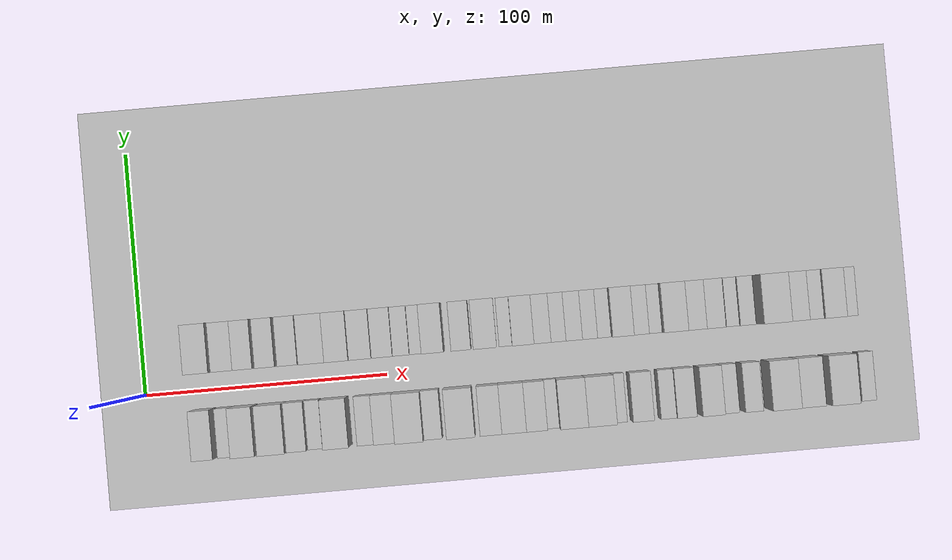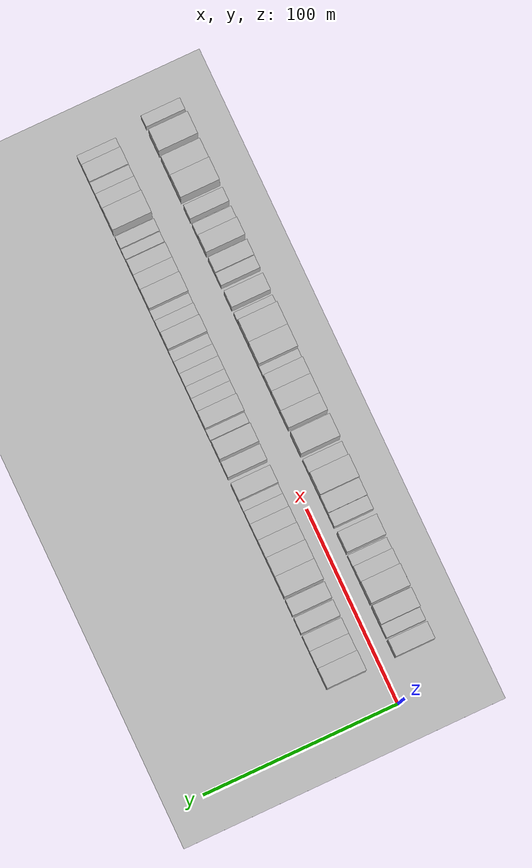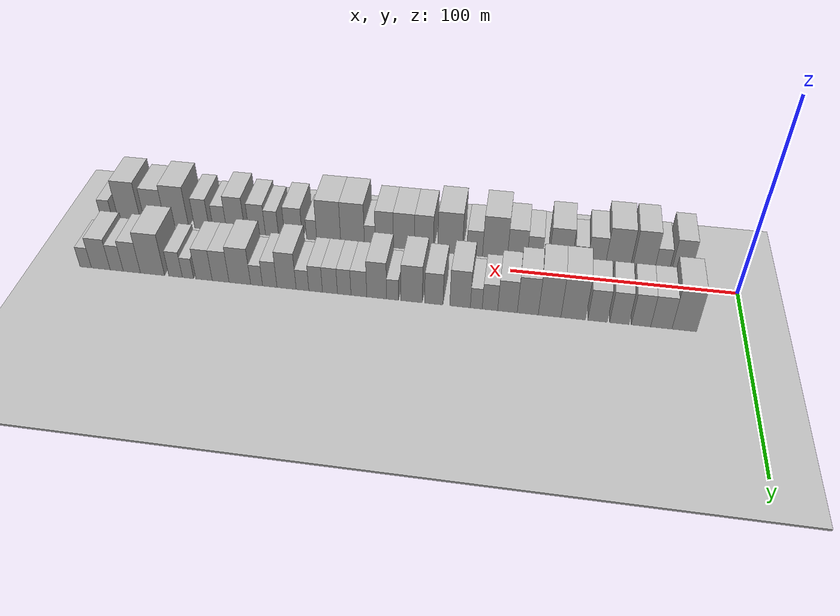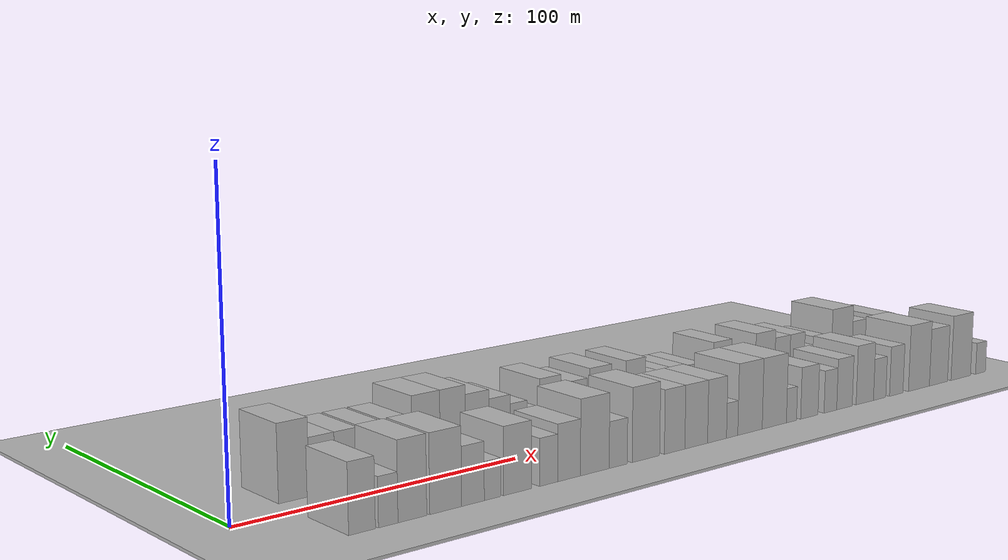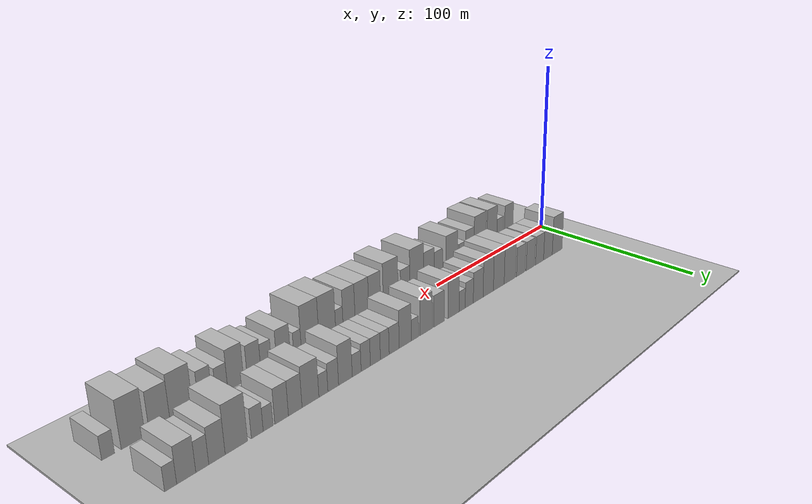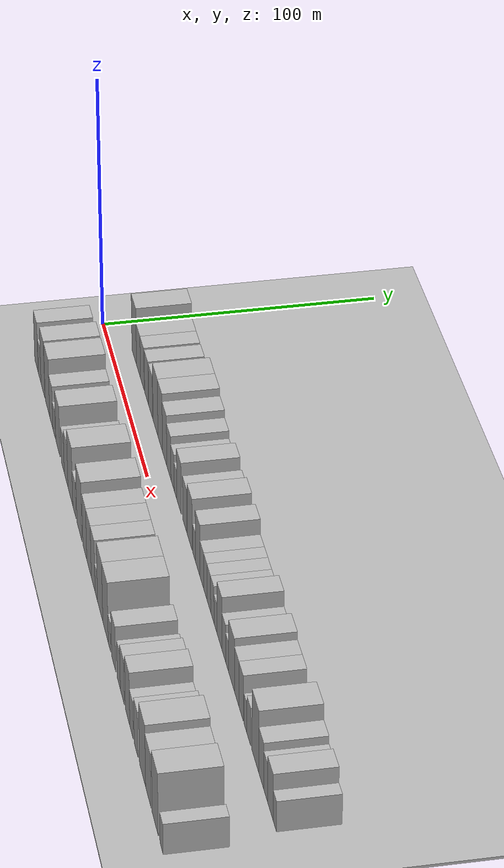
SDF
<?xml version="1.0" encoding="utf-8"?>

<sdf version="1.6">

   <world name="default">

      <gui fullscreen="0">

         <camera name="user_camera">

            <pose>-15 0 4.57585 0 0 0</pose>

            <view_controller>orbit</view_controller>

         </camera>

      </gui>

      <scene>

         <sky>

           <clouds>

             <speed>12</speed>

           </clouds>

         </sky>

         <ambient>0.4 0.4 0.4 1</ambient>

         <background>0.7 0.7 0.7 1</background>

         <shadows>1</shadows>

      </scene>

      <gravity>0 0 -9.8066</gravity>

      <magnetic_field>6e-06 2.3e-05 -4.2e-05</magnetic_field>

      <physics default="0" name="default_physics" type="ode">

         <ode>

            <solver>

               <type>quick</type>

               <iters>10</iters>

               <sor>1.0</sor>

               <use_dynamic_moi_rescaling>0</use_dynamic_moi_rescaling>

            </solver>

            <constraints>

               <cfm>0</cfm>

               <erp>0.2</erp>

               <contact_max_correcting_vel>100</contact_max_correcting_vel>

               <contact_surface_layer>0.001</contact_surface_layer>

            </constraints>

         </ode>

         <max_step_size>0.004</max_step_size>

         <real_time_factor>1</real_time_factor>

         <real_time_update_rate>250</real_time_update_rate>

      </physics>

      <light name="sun" type="directional">

         <cast_shadows>1</cast_shadows>

         <pose>0 0 10 0 0 0</pose>

         <diffuse>0.8 0.8 0.8 1</diffuse>

         <specular>0.2 0.2 0.2 1</specular>

         <attenuation>

            <range>1000</range>

            <constant>0.9</constant>

            <linear>0.01</linear>

            <quadratic>0.001</quadratic>

         </attenuation>

         <direction>-0.5 0.1 -0.9</direction>

      </light>

      <include>

         <name>ground_plane_1</name>

         <uri>model://HANNAS_ground_plane</uri>

         <pose>0 0 0  0 0 0</pose>

      </include>

      <include>

         <name>ground_plane_2</name>

         <uri>model://HANNAS_ground_plane</uri>

         <pose>100 0 0  0 0 0</pose>

      </include>

      <model name="building_1">

         <static>1</static>

         <pose frame="">25.0952 17.5000 0 0.000000 0.000000 1.570796</pose>

         <link name="link">

            <pose frame="">0 0 12.00 0 0 0</pose>

            <collision name="collision">

               <geometry>

                  <box>

                     <size>20.0000 10.1904 24.0000</size>

                  </box>

               </geometry>

               <max_contacts>10</max_contacts>

               <surface>

                  <contact>

                     <ode/>

                  </contact>

                  <bounce/>

                  <friction>

                     <torsional>

                        <ode/>

                     </torsional>

                     <ode/>

                  </friction>

               </surface>

            </collision>

            <visual name="visual">

               <cast_shadows>0</cast_shadows>

               <geometry>

                  <box>

                     <size>20.0000 10.1904 24.0000</size>

                  </box>

               </geometry>

               <material>

                  <script>

                     <uri>model://HANNAS_wall/materials/scripts</uri>

                     <uri>model://HANNAS_wall/materials/textures</uri>

                     <name>vrc/HANNAS_wall</name>

                  </script>

               </material>

            </visual>

            <self_collide>0</self_collide>

            <enable_wind>0</enable_wind>

            <kinematic>0</kinematic>

         </link>

      </model>

      <model name="building_2">

         <static>1</static>

         <pose frame="">34.6086 17.5000 0 0.000000 0.000000 1.570796</pose>

         <link name="link">

            <pose frame="">0 0 9.00 0 0 0</pose>

            <collision name="collision">

               <geometry>

                  <box>

                     <size>20.0000 8.8364 18.0000</size>

                  </box>

               </geometry>

               <max_contacts>10</max_contacts>

               <surface>

                  <contact>

                     <ode/>

                  </contact>

                  <bounce/>

                  <friction>

                     <torsional>

                        <ode/>

                     </torsional>

                     <ode/>

                  </friction>

               </surface>

            </collision>

            <visual name="visual">

               <cast_shadows>0</cast_shadows>

               <geometry>

                  <box>

                     <size>20.0000 8.8364 18.0000</size>

                  </box>

               </geometry>

               <material>

                  <script>

                     <uri>model://HANNAS_wall/materials/scripts</uri>

                     <uri>model://HANNAS_wall/materials/textures</uri>

                     <name>vrc/HANNAS_wall</name>

                  </script>

               </material>

            </visual>

            <self_collide>0</self_collide>

            <enable_wind>0</enable_wind>

            <kinematic>0</kinematic>

         </link>

      </model>

      <model name="building_3">

         <static>1</static>

         <pose frame="">43.0522 17.5000 0 0.000000 0.000000 1.570796</pose>

         <link name="link">

            <pose frame="">0 0 9.00 0 0 0</pose>

            <collision name="collision">

               <geometry>

                  <box>

                     <size>20.0000 8.0508 18.0000</size>

                  </box>

               </geometry>

               <max_contacts>10</max_contacts>

               <surface>

                  <contact>

                     <ode/>

                  </contact>

                  <bounce/>

                  <friction>

                     <torsional>

                        <ode/>

                     </torsional>

                     <ode/>

                  </friction>

               </surface>

            </collision>

            <visual name="visual">

               <cast_shadows>0</cast_shadows>

               <geometry>

                  <box>

                     <size>20.0000 8.0508 18.0000</size>

                  </box>

               </geometry>

               <material>

                  <script>

                     <uri>model://HANNAS_wall/materials/scripts</uri>

                     <uri>model://HANNAS_wall/materials/textures</uri>

                     <name>vrc/HANNAS_wall</name>

                  </script>

               </material>

            </visual>

            <self_collide>0</self_collide>

            <enable_wind>0</enable_wind>

            <kinematic>0</kinematic>

         </link>

      </model>

      <model name="building_4">

         <static>1</static>

         <pose frame="">52.1330 17.5000 0 0.000000 0.000000 1.570796</pose>

         <link name="link">

            <pose frame="">0 0 9.00 0 0 0</pose>

            <collision name="collision">

               <geometry>

                  <box>

                     <size>20.0000 8.1108 18.0000</size>

                  </box>

               </geometry>

               <max_contacts>10</max_contacts>

               <surface>

                  <contact>

                     <ode/>

                  </contact>

                  <bounce/>

                  <friction>

                     <torsional>

                        <ode/>

                     </torsional>

                     <ode/>

                  </friction>

               </surface>

            </collision>

            <visual name="visual">

               <cast_shadows>0</cast_shadows>

               <geometry>

                  <box>

                     <size>20.0000 8.1108 18.0000</size>

                  </box>

               </geometry>

               <material>

                  <script>

                     <uri>model://HANNAS_wall/materials/scripts</uri>

                     <uri>model://HANNAS_wall/materials/textures</uri>

                     <name>vrc/HANNAS_wall</name>

                  </script>

               </material>

            </visual>

            <self_collide>0</self_collide>

            <enable_wind>0</enable_wind>

            <kinematic>0</kinematic>

         </link>

      </model>

      <model name="building_5">

         <static>1</static>

         <pose frame="">61.3012 17.5000 0 0.000000 0.000000 1.570796</pose>

         <link name="link">

            <pose frame="">0 0 9.00 0 0 0</pose>

            <collision name="collision">

               <geometry>

                  <box>

                     <size>20.0000 8.2256 18.0000</size>

                  </box>

               </geometry>

               <max_contacts>10</max_contacts>

               <surface>

                  <contact>

                     <ode/>

                  </contact>

                  <bounce/>

                  <friction>

                     <torsional>

                        <ode/>

                     </torsional>

                     <ode/>

                  </friction>

               </surface>

            </collision>

            <visual name="visual">

               <cast_shadows>0</cast_shadows>

               <geometry>

                  <box>

                     <size>20.0000 8.2256 18.0000</size>

                  </box>

               </geometry>

               <material>

                  <script>

                     <uri>model://HANNAS_wall/materials/scripts</uri>

                     <uri>model://HANNAS_wall/materials/textures</uri>

                     <name>vrc/HANNAS_wall</name>

                  </script>

               </material>

            </visual>

            <self_collide>0</self_collide>

            <enable_wind>0</enable_wind>

            <kinematic>0</kinematic>

         </link>

      </model>

      <model name="building_6">

         <static>1</static>

         <pose frame="">71.6236 17.5000 0 0.000000 0.000000 1.570796</pose>

         <link name="link">

            <pose frame="">0 0 12.00 0 0 0</pose>

            <collision name="collision">

               <geometry>

                  <box>

                     <size>20.0000 10.4191 24.0000</size>

                  </box>

               </geometry>

               <max_contacts>10</max_contacts>

               <surface>

                  <contact>

                     <ode/>

                  </contact>

                  <bounce/>

                  <friction>

                     <torsional>

                        <ode/>

                     </torsional>

                     <ode/>

                  </friction>

               </surface>

            </collision>

            <visual name="visual">

               <cast_shadows>0</cast_shadows>

               <geometry>

                  <box>

                     <size>20.0000 10.4191 24.0000</size>

                  </box>

               </geometry>

               <material>

                  <script>

                     <uri>model://HANNAS_wall/materials/scripts</uri>

                     <uri>model://HANNAS_wall/materials/textures</uri>

                     <name>vrc/HANNAS_wall</name>

                  </script>

               </material>

            </visual>

            <self_collide>0</self_collide>

            <enable_wind>0</enable_wind>

            <kinematic>0</kinematic>

         </link>

      </model>

      <model name="building_7">

         <static>1</static>

         <pose frame="">81.6582 17.5000 0 0.000000 0.000000 1.570796</pose>

         <link name="link">

            <pose frame="">0 0 12.00 0 0 0</pose>

            <collision name="collision">

               <geometry>

                  <box>

                     <size>20.0000 9.6503 24.0000</size>

                  </box>

               </geometry>

               <max_contacts>10</max_contacts>

               <surface>

                  <contact>

                     <ode/>

                  </contact>

                  <bounce/>

                  <friction>

                     <torsional>

                        <ode/>

                     </torsional>

                     <ode/>

                  </friction>

               </surface>

            </collision>

            <visual name="visual">

               <cast_shadows>0</cast_shadows>

               <geometry>

                  <box>

                     <size>20.0000 9.6503 24.0000</size>

                  </box>

               </geometry>

               <material>

                  <script>

                     <uri>model://HANNAS_wall/materials/scripts</uri>

                     <uri>model://HANNAS_wall/materials/textures</uri>

                     <name>vrc/HANNAS_wall</name>

                  </script>

               </material>

            </visual>

            <self_collide>0</self_collide>

            <enable_wind>0</enable_wind>

            <kinematic>0</kinematic>

         </link>

      </model>

      <model name="building_8">

         <static>1</static>

         <pose frame="">91.0004 17.5000 0 0.000000 0.000000 1.570796</pose>

         <link name="link">

            <pose frame="">0 0 10.50 0 0 0</pose>

            <collision name="collision">

               <geometry>

                  <box>

                     <size>20.0000 9.0341 21.0000</size>

                  </box>

               </geometry>

               <max_contacts>10</max_contacts>

               <surface>

                  <contact>

                     <ode/>

                  </contact>

                  <bounce/>

                  <friction>

                     <torsional>

                        <ode/>

                     </torsional>

                     <ode/>

                  </friction>

               </surface>

            </collision>

            <visual name="visual">

               <cast_shadows>0</cast_shadows>

               <geometry>

                  <box>

                     <size>20.0000 9.0341 21.0000</size>

                  </box>

               </geometry>

               <material>

                  <script>

                     <uri>model://HANNAS_wall/materials/scripts</uri>

                     <uri>model://HANNAS_wall/materials/textures</uri>

                     <name>vrc/HANNAS_wall</name>

                  </script>

               </material>

            </visual>

            <self_collide>0</self_collide>

            <enable_wind>0</enable_wind>

            <kinematic>0</kinematic>

         </link>

      </model>

      <model name="building_9">

         <static>1</static>

         <pose frame="">99.7317 17.5000 0 0.000000 0.000000 1.570796</pose>

         <link name="link">

            <pose frame="">0 0 9.00 0 0 0</pose>

            <collision name="collision">

               <geometry>

                  <box>

                     <size>20.0000 8.4285 18.0000</size>

                  </box>

               </geometry>

               <max_contacts>10</max_contacts>

               <surface>

                  <contact>

                     <ode/>

                  </contact>

                  <bounce/>

                  <friction>

                     <torsional>

                        <ode/>

                     </torsional>

                     <ode/>

                  </friction>

               </surface>

            </collision>

            <visual name="visual">

               <cast_shadows>0</cast_shadows>

               <geometry>

                  <box>

                     <size>20.0000 8.4285 18.0000</size>

                  </box>

               </geometry>

               <material>

                  <script>

                     <uri>model://HANNAS_wall/materials/scripts</uri>

                     <uri>model://HANNAS_wall/materials/textures</uri>

                     <name>vrc/HANNAS_wall</name>

                  </script>

               </material>

            </visual>

            <self_collide>0</self_collide>

            <enable_wind>0</enable_wind>

            <kinematic>0</kinematic>

         </link>

      </model>

      <model name="building_10">

         <static>1</static>

         <pose frame="">107.3018 17.5000 0 0.000000 0.000000 1.570796</pose>

         <link name="link">

            <pose frame="">0 0 7.50 0 0 0</pose>

            <collision name="collision">

               <geometry>

                  <box>

                     <size>20.0000 6.7117 15.0000</size>

                  </box>

               </geometry>

               <max_contacts>10</max_contacts>

               <surface>

                  <contact>

                     <ode/>

                  </contact>

                  <bounce/>

                  <friction>

                     <torsional>

                        <ode/>

                     </torsional>

                     <ode/>

                  </friction>

               </surface>

            </collision>

            <visual name="visual">

               <cast_shadows>0</cast_shadows>

               <geometry>

                  <box>

                     <size>20.0000 6.7117 15.0000</size>

                  </box>

               </geometry>

               <material>

                  <script>

                     <uri>model://HANNAS_wall/materials/scripts</uri>

                     <uri>model://HANNAS_wall/materials/textures</uri>

                     <name>vrc/HANNAS_wall</name>

                  </script>

               </material>

            </visual>

            <self_collide>0</self_collide>

            <enable_wind>0</enable_wind>

            <kinematic>0</kinematic>

         </link>

      </model>

      <model name="building_11">

         <static>1</static>

         <pose frame="">113.2352 17.5000 0 0.000000 0.000000 1.570796</pose>

         <link name="link">

            <pose frame="">0 0 6.00 0 0 0</pose>

            <collision name="collision">

               <geometry>

                  <box>

                     <size>20.0000 5.1550 12.0000</size>

                  </box>

               </geometry>

               <max_contacts>10</max_contacts>

               <surface>

                  <contact>

                     <ode/>

                  </contact>

                  <bounce/>

                  <friction>

                     <torsional>

                        <ode/>

                     </torsional>

                     <ode/>

                  </friction>

               </surface>

            </collision>

            <visual name="visual">

               <cast_shadows>0</cast_shadows>

               <geometry>

                  <box>

                     <size>20.0000 5.1550 12.0000</size>

                  </box>

               </geometry>

               <material>

                  <script>

                     <uri>model://HANNAS_wall/materials/scripts</uri>

                     <uri>model://HANNAS_wall/materials/textures</uri>

                     <name>vrc/HANNAS_wall</name>

                  </script>

               </material>

            </visual>

            <self_collide>0</self_collide>

            <enable_wind>0</enable_wind>

            <kinematic>0</kinematic>

         </link>

      </model>

      <model name="building_12">

         <static>1</static>

         <pose frame="">120.2897 17.5000 0 0.000000 0.000000 1.570796</pose>

         <link name="link">

            <pose frame="">0 0 10.50 0 0 0</pose>

            <collision name="collision">

               <geometry>

                  <box>

                     <size>20.0000 8.9539 21.0000</size>

                  </box>

               </geometry>

               <max_contacts>10</max_contacts>

               <surface>

                  <contact>

                     <ode/>

                  </contact>

                  <bounce/>

                  <friction>

                     <torsional>

                        <ode/>

                     </torsional>

                     <ode/>

                  </friction>

               </surface>

            </collision>

            <visual name="visual">

               <cast_shadows>0</cast_shadows>

               <geometry>

                  <box>

                     <size>20.0000 8.9539 21.0000</size>

                  </box>

               </geometry>

               <material>

                  <script>

                     <uri>model://HANNAS_wall/materials/scripts</uri>

                     <uri>model://HANNAS_wall/materials/textures</uri>

                     <name>vrc/HANNAS_wall</name>

                  </script>

               </material>

            </visual>

            <self_collide>0</self_collide>

            <enable_wind>0</enable_wind>

            <kinematic>0</kinematic>

         </link>

      </model>

      <model name="building_13">

         <static>1</static>

         <pose frame="">131.7899 17.5000 0 0.000000 0.000000 1.570796</pose>

         <link name="link">

            <pose frame="">0 0 9.00 0 0 0</pose>

            <collision name="collision">

               <geometry>

                  <box>

                     <size>20.0000 8.0466 18.0000</size>

                  </box>

               </geometry>

               <max_contacts>10</max_contacts>

               <surface>

                  <contact>

                     <ode/>

                  </contact>

                  <bounce/>

                  <friction>

                     <torsional>

                        <ode/>

                     </torsional>

                     <ode/>

                  </friction>

               </surface>

            </collision>

            <visual name="visual">

               <cast_shadows>0</cast_shadows>

               <geometry>

                  <box>

                     <size>20.0000 8.0466 18.0000</size>

                  </box>

               </geometry>

               <material>

                  <script>

                     <uri>model://HANNAS_wall/materials/scripts</uri>

                     <uri>model://HANNAS_wall/materials/textures</uri>

                     <name>vrc/HANNAS_wall</name>

                  </script>

               </material>

            </visual>

            <self_collide>0</self_collide>

            <enable_wind>0</enable_wind>

            <kinematic>0</kinematic>

         </link>

      </model>

      <model name="building_14">

         <static>1</static>

         <pose frame="">141.5493 17.5000 0 0.000000 0.000000 1.570796</pose>

         <link name="link">

            <pose frame="">0 0 10.50 0 0 0</pose>

            <collision name="collision">

               <geometry>

                  <box>

                     <size>20.0000 9.4722 21.0000</size>

                  </box>

               </geometry>

               <max_contacts>10</max_contacts>

               <surface>

                  <contact>

                     <ode/>

                  </contact>

                  <bounce/>

                  <friction>

                     <torsional>

                        <ode/>

                     </torsional>

                     <ode/>

                  </friction>

               </surface>

            </collision>

            <visual name="visual">

               <cast_shadows>0</cast_shadows>

               <geometry>

                  <box>

                     <size>20.0000 9.4722 21.0000</size>

                  </box>

               </geometry>

               <material>

                  <script>

                     <uri>model://HANNAS_wall/materials/scripts</uri>

                     <uri>model://HANNAS_wall/materials/textures</uri>

                     <name>vrc/HANNAS_wall</name>

                  </script>

               </material>

            </visual>

            <self_collide>0</self_collide>

            <enable_wind>0</enable_wind>

            <kinematic>0</kinematic>

         </link>

      </model>

      <model name="building_15">

         <static>1</static>

         <pose frame="">149.9510 17.5000 0 0.000000 0.000000 1.570796</pose>

         <link name="link">

            <pose frame="">0 0 6.00 0 0 0</pose>

            <collision name="collision">

               <geometry>

                  <box>

                     <size>20.0000 5.3313 12.0000</size>

                  </box>

               </geometry>

               <max_contacts>10</max_contacts>

               <surface>

                  <contact>

                     <ode/>

                  </contact>

                  <bounce/>

                  <friction>

                     <torsional>

                        <ode/>

                     </torsional>

                     <ode/>

                  </friction>

               </surface>

            </collision>

            <visual name="visual">

               <cast_shadows>0</cast_shadows>

               <geometry>

                  <box>

                     <size>20.0000 5.3313 12.0000</size>

                  </box>

               </geometry>

               <material>

                  <script>

                     <uri>model://HANNAS_wall/materials/scripts</uri>

                     <uri>model://HANNAS_wall/materials/textures</uri>

                     <name>vrc/HANNAS_wall</name>

                  </script>

               </material>

            </visual>

            <self_collide>0</self_collide>

            <enable_wind>0</enable_wind>

            <kinematic>0</kinematic>

         </link>

      </model>

      <model name="building_16">

         <static>1</static>

         <pose frame="">157.0202 17.5000 0 0.000000 0.000000 1.570796</pose>

         <link name="link">

            <pose frame="">0 0 10.50 0 0 0</pose>

            <collision name="collision">

               <geometry>

                  <box>

                     <size>20.0000 8.8071 21.0000</size>

                  </box>

               </geometry>

               <max_contacts>10</max_contacts>

               <surface>

                  <contact>

                     <ode/>

                  </contact>

                  <bounce/>

                  <friction>

                     <torsional>

                        <ode/>

                     </torsional>

                     <ode/>

                  </friction>

               </surface>

            </collision>

            <visual name="visual">

               <cast_shadows>0</cast_shadows>

               <geometry>

                  <box>

                     <size>20.0000 8.8071 21.0000</size>

                  </box>

               </geometry>

               <material>

                  <script>

                     <uri>model://HANNAS_wall/materials/scripts</uri>

                     <uri>model://HANNAS_wall/materials/textures</uri>

                     <name>vrc/HANNAS_wall</name>

                  </script>

               </material>

            </visual>

            <self_collide>0</self_collide>

            <enable_wind>0</enable_wind>

            <kinematic>0</kinematic>

         </link>

      </model>

      <model name="building_17">

         <static>1</static>

         <pose frame="">164.9590 17.5000 0 0.000000 0.000000 1.570796</pose>

         <link name="link">

            <pose frame="">0 0 7.50 0 0 0</pose>

            <collision name="collision">

               <geometry>

                  <box>

                     <size>20.0000 7.0706 15.0000</size>

                  </box>

               </geometry>

               <max_contacts>10</max_contacts>

               <surface>

                  <contact>

                     <ode/>

                  </contact>

                  <bounce/>

                  <friction>

                     <torsional>

                        <ode/>

                     </torsional>

                     <ode/>

                  </friction>

               </surface>

            </collision>

            <visual name="visual">

               <cast_shadows>0</cast_shadows>

               <geometry>

                  <box>

                     <size>20.0000 7.0706 15.0000</size>

                  </box>

               </geometry>

               <material>

                  <script>

                     <uri>model://HANNAS_wall/materials/scripts</uri>

                     <uri>model://HANNAS_wall/materials/textures</uri>

                     <name>vrc/HANNAS_wall</name>

                  </script>

               </material>

            </visual>

            <self_collide>0</self_collide>

            <enable_wind>0</enable_wind>

            <kinematic>0</kinematic>

         </link>

      </model>

      <model name="building_18">

         <static>1</static>

         <pose frame="">171.5373 17.5000 0 0.000000 0.000000 1.570796</pose>

         <link name="link">

            <pose frame="">0 0 7.50 0 0 0</pose>

            <collision name="collision">

               <geometry>

                  <box>

                     <size>20.0000 6.0860 15.0000</size>

                  </box>

               </geometry>

               <max_contacts>10</max_contacts>

               <surface>

                  <contact>

                     <ode/>

                  </contact>

                  <bounce/>

                  <friction>

                     <torsional>

                        <ode/>

                     </torsional>

                     <ode/>

                  </friction>

               </surface>

            </collision>

            <visual name="visual">

               <cast_shadows>0</cast_shadows>

               <geometry>

                  <box>

                     <size>20.0000 6.0860 15.0000</size>

                  </box>

               </geometry>

               <material>

                  <script>

                     <uri>model://HANNAS_wall/materials/scripts</uri>

                     <uri>model://HANNAS_wall/materials/textures</uri>

                     <name>vrc/HANNAS_wall</name>

                  </script>

               </material>

            </visual>

            <self_collide>0</self_collide>

            <enable_wind>0</enable_wind>

            <kinematic>0</kinematic>

         </link>

      </model>

      <model name="building_19">

         <static>1</static>

         <pose frame="">177.9470 17.5000 0 0.000000 0.000000 1.570796</pose>

         <link name="link">

            <pose frame="">0 0 7.50 0 0 0</pose>

            <collision name="collision">

               <geometry>

                  <box>

                     <size>20.0000 6.7334 15.0000</size>

                  </box>

               </geometry>

               <max_contacts>10</max_contacts>

               <surface>

                  <contact>

                     <ode/>

                  </contact>

                  <bounce/>

                  <friction>

                     <torsional>

                        <ode/>

                     </torsional>

                     <ode/>

                  </friction>

               </surface>

            </collision>

            <visual name="visual">

               <cast_shadows>0</cast_shadows>

               <geometry>

                  <box>

                     <size>20.0000 6.7334 15.0000</size>

                  </box>

               </geometry>

               <material>

                  <script>

                     <uri>model://HANNAS_wall/materials/scripts</uri>

                     <uri>model://HANNAS_wall/materials/textures</uri>

                     <name>vrc/HANNAS_wall</name>

                  </script>

               </material>

            </visual>

            <self_collide>0</self_collide>

            <enable_wind>0</enable_wind>

            <kinematic>0</kinematic>

         </link>

      </model>

      <model name="building_20">

         <static>1</static>

         <pose frame="">184.3895 17.5000 0 0.000000 0.000000 1.570796</pose>

         <link name="link">

            <pose frame="">0 0 7.50 0 0 0</pose>

            <collision name="collision">

               <geometry>

                  <box>

                     <size>20.0000 6.1515 15.0000</size>

                  </box>

               </geometry>

               <max_contacts>10</max_contacts>

               <surface>

                  <contact>

                     <ode/>

                  </contact>

                  <bounce/>

                  <friction>

                     <torsional>

                        <ode/>

                     </torsional>

                     <ode/>

                  </friction>

               </surface>

            </collision>

            <visual name="visual">

               <cast_shadows>0</cast_shadows>

               <geometry>

                  <box>

                     <size>20.0000 6.1515 15.0000</size>

                  </box>

               </geometry>

               <material>

                  <script>

                     <uri>model://HANNAS_wall/materials/scripts</uri>

                     <uri>model://HANNAS_wall/materials/textures</uri>

                     <name>vrc/HANNAS_wall</name>

                  </script>

               </material>

            </visual>

            <self_collide>0</self_collide>

            <enable_wind>0</enable_wind>

            <kinematic>0</kinematic>

         </link>

      </model>

      <model name="building_21">

         <static>1</static>

         <pose frame="">190.3441 17.5000 0 0.000000 0.000000 1.570796</pose>

         <link name="link">

            <pose frame="">0 0 6.00 0 0 0</pose>

            <collision name="collision">

               <geometry>

                  <box>

                     <size>20.0000 5.7578 12.0000</size>

                  </box>

               </geometry>

               <max_contacts>10</max_contacts>

               <surface>

                  <contact>

                     <ode/>

                  </contact>

                  <bounce/>

                  <friction>

                     <torsional>

                        <ode/>

                     </torsional>

                     <ode/>

                  </friction>

               </surface>

            </collision>

            <visual name="visual">

               <cast_shadows>0</cast_shadows>

               <geometry>

                  <box>

                     <size>20.0000 5.7578 12.0000</size>

                  </box>

               </geometry>

               <material>

                  <script>

                     <uri>model://HANNAS_wall/materials/scripts</uri>

                     <uri>model://HANNAS_wall/materials/textures</uri>

                     <name>vrc/HANNAS_wall</name>

                  </script>

               </material>

            </visual>

            <self_collide>0</self_collide>

            <enable_wind>0</enable_wind>

            <kinematic>0</kinematic>

         </link>

      </model>

      <model name="building_22">

         <static>1</static>

         <pose frame="">197.5777 17.5000 0 0.000000 0.000000 1.570796</pose>

         <link name="link">

            <pose frame="">0 0 10.50 0 0 0</pose>

            <collision name="collision">

               <geometry>

                  <box>

                     <size>20.0000 8.7095 21.0000</size>

                  </box>

               </geometry>

               <max_contacts>10</max_contacts>

               <surface>

                  <contact>

                     <ode/>

                  </contact>

                  <bounce/>

                  <friction>

                     <torsional>

                        <ode/>

                     </torsional>

                     <ode/>

                  </friction>

               </surface>

            </collision>

            <visual name="visual">

               <cast_shadows>0</cast_shadows>

               <geometry>

                  <box>

                     <size>20.0000 8.7095 21.0000</size>

                  </box>

               </geometry>

               <material>

                  <script>

                     <uri>model://HANNAS_wall/materials/scripts</uri>

                     <uri>model://HANNAS_wall/materials/textures</uri>

                     <name>vrc/HANNAS_wall</name>

                  </script>

               </material>

            </visual>

            <self_collide>0</self_collide>

            <enable_wind>0</enable_wind>

            <kinematic>0</kinematic>

         </link>

      </model>

      <model name="building_23">

         <static>1</static>

         <pose frame="">205.2382 17.5000 0 0.000000 0.000000 1.570796</pose>

         <link name="link">

            <pose frame="">0 0 7.50 0 0 0</pose>

            <collision name="collision">

               <geometry>

                  <box>

                     <size>20.0000 6.6115 15.0000</size>

                  </box>

               </geometry>

               <max_contacts>10</max_contacts>

               <surface>

                  <contact>

                     <ode/>

                  </contact>

                  <bounce/>

                  <friction>

                     <torsional>

                        <ode/>

                     </torsional>

                     <ode/>

                  </friction>

               </surface>

            </collision>

            <visual name="visual">

               <cast_shadows>0</cast_shadows>

               <geometry>

                  <box>

                     <size>20.0000 6.6115 15.0000</size>

                  </box>

               </geometry>

               <material>

                  <script>

                     <uri>model://HANNAS_wall/materials/scripts</uri>

                     <uri>model://HANNAS_wall/materials/textures</uri>

                     <name>vrc/HANNAS_wall</name>

                  </script>

               </material>

            </visual>

            <self_collide>0</self_collide>

            <enable_wind>0</enable_wind>

            <kinematic>0</kinematic>

         </link>

      </model>

      <model name="building_24">

         <static>1</static>

         <pose frame="">211.2773 17.5000 0 0.000000 0.000000 1.570796</pose>

         <link name="link">

            <pose frame="">0 0 6.00 0 0 0</pose>

            <collision name="collision">

               <geometry>

                  <box>

                     <size>20.0000 5.4667 12.0000</size>

                  </box>

               </geometry>

               <max_contacts>10</max_contacts>

               <surface>

                  <contact>

                     <ode/>

                  </contact>

                  <bounce/>

                  <friction>

                     <torsional>

                        <ode/>

                     </torsional>

                     <ode/>

                  </friction>

               </surface>

            </collision>

            <visual name="visual">

               <cast_shadows>0</cast_shadows>

               <geometry>

                  <box>

                     <size>20.0000 5.4667 12.0000</size>

                  </box>

               </geometry>

               <material>

                  <script>

                     <uri>model://HANNAS_wall/materials/scripts</uri>

                     <uri>model://HANNAS_wall/materials/textures</uri>

                     <name>vrc/HANNAS_wall</name>

                  </script>

               </material>

            </visual>

            <self_collide>0</self_collide>

            <enable_wind>0</enable_wind>

            <kinematic>0</kinematic>

         </link>

      </model>

      <model name="building_25">

         <static>1</static>

         <pose frame="">218.9881 17.5000 0 0.000000 0.000000 1.570796</pose>

         <link name="link">

            <pose frame="">0 0 10.50 0 0 0</pose>

            <collision name="collision">

               <geometry>

                  <box>

                     <size>20.0000 9.9550 21.0000</size>

                  </box>

               </geometry>

               <max_contacts>10</max_contacts>

               <surface>

                  <contact>

                     <ode/>

                  </contact>

                  <bounce/>

                  <friction>

                     <torsional>

                        <ode/>

                     </torsional>

                     <ode/>

                  </friction>

               </surface>

            </collision>

            <visual name="visual">

               <cast_shadows>0</cast_shadows>

               <geometry>

                  <box>

                     <size>20.0000 9.9550 21.0000</size>

                  </box>

               </geometry>

               <material>

                  <script>

                     <uri>model://HANNAS_wall/materials/scripts</uri>

                     <uri>model://HANNAS_wall/materials/textures</uri>

                     <name>vrc/HANNAS_wall</name>

                  </script>

               </material>

            </visual>

            <self_collide>0</self_collide>

            <enable_wind>0</enable_wind>

            <kinematic>0</kinematic>

         </link>

      </model>

      <model name="building_26">

         <static>1</static>

         <pose frame="">227.8656 17.5000 0 0.000000 0.000000 1.570796</pose>

         <link name="link">

            <pose frame="">0 0 9.00 0 0 0</pose>

            <collision name="collision">

               <geometry>

                  <box>

                     <size>20.0000 7.7998 18.0000</size>

                  </box>

               </geometry>

               <max_contacts>10</max_contacts>

               <surface>

                  <contact>

                     <ode/>

                  </contact>

                  <bounce/>

                  <friction>

                     <torsional>

                        <ode/>

                     </torsional>

                     <ode/>

                  </friction>

               </surface>

            </collision>

            <visual name="visual">

               <cast_shadows>0</cast_shadows>

               <geometry>

                  <box>

                     <size>20.0000 7.7998 18.0000</size>

                  </box>

               </geometry>

               <material>

                  <script>

                     <uri>model://HANNAS_wall/materials/scripts</uri>

                     <uri>model://HANNAS_wall/materials/textures</uri>

                     <name>vrc/HANNAS_wall</name>

                  </script>

               </material>

            </visual>

            <self_collide>0</self_collide>

            <enable_wind>0</enable_wind>

            <kinematic>0</kinematic>

         </link>

      </model>

      <model name="building_27">

         <static>1</static>

         <pose frame="">235.5774 17.5000 0 0.000000 0.000000 1.570796</pose>

         <link name="link">

            <pose frame="">0 0 9.00 0 0 0</pose>

            <collision name="collision">

               <geometry>

                  <box>

                     <size>20.0000 7.6239 18.0000</size>

                  </box>

               </geometry>

               <max_contacts>10</max_contacts>

               <surface>

                  <contact>

                     <ode/>

                  </contact>

                  <bounce/>

                  <friction>

                     <torsional>

                        <ode/>

                     </torsional>

                     <ode/>

                  </friction>

               </surface>

            </collision>

            <visual name="visual">

               <cast_shadows>0</cast_shadows>

               <geometry>

                  <box>

                     <size>20.0000 7.6239 18.0000</size>

                  </box>

               </geometry>

               <material>

                  <script>

                     <uri>model://HANNAS_wall/materials/scripts</uri>

                     <uri>model://HANNAS_wall/materials/textures</uri>

                     <name>vrc/HANNAS_wall</name>

                  </script>

               </material>

            </visual>

            <self_collide>0</self_collide>

            <enable_wind>0</enable_wind>

            <kinematic>0</kinematic>

         </link>

      </model>

      <model name="building_28">

         <static>1</static>

         <pose frame="">243.0308 17.5000 0 0.000000 0.000000 1.570796</pose>

         <link name="link">

            <pose frame="">0 0 6.00 0 0 0</pose>

            <collision name="collision">

               <geometry>

                  <box>

                     <size>20.0000 5.2829 12.0000</size>

                  </box>

               </geometry>

               <max_contacts>10</max_contacts>

               <surface>

                  <contact>

                     <ode/>

                  </contact>

                  <bounce/>

                  <friction>

                     <torsional>

                        <ode/>

                     </torsional>

                     <ode/>

                  </friction>

               </surface>

            </collision>

            <visual name="visual">

               <cast_shadows>0</cast_shadows>

               <geometry>

                  <box>

                     <size>20.0000 5.2829 12.0000</size>

                  </box>

               </geometry>

               <material>

                  <script>

                     <uri>model://HANNAS_wall/materials/scripts</uri>

                     <uri>model://HANNAS_wall/materials/textures</uri>

                     <name>vrc/HANNAS_wall</name>

                  </script>

               </material>

            </visual>

            <self_collide>0</self_collide>

            <enable_wind>0</enable_wind>

            <kinematic>0</kinematic>

         </link>

      </model>

      <model name="building_29">

         <static>1</static>

         <pose frame="">248.8422 17.5000 0 0.000000 0.000000 1.570796</pose>

         <link name="link">

            <pose frame="">0 0 7.50 0 0 0</pose>

            <collision name="collision">

               <geometry>

                  <box>

                     <size>20.0000 6.3400 15.0000</size>

                  </box>

               </geometry>

               <max_contacts>10</max_contacts>

               <surface>

                  <contact>

                     <ode/>

                  </contact>

                  <bounce/>

                  <friction>

                     <torsional>

                        <ode/>

                     </torsional>

                     <ode/>

                  </friction>

               </surface>

            </collision>

            <visual name="visual">

               <cast_shadows>0</cast_shadows>

               <geometry>

                  <box>

                     <size>20.0000 6.3400 15.0000</size>

                  </box>

               </geometry>

               <material>

                  <script>

                     <uri>model://HANNAS_wall/materials/scripts</uri>

                     <uri>model://HANNAS_wall/materials/textures</uri>

                     <name>vrc/HANNAS_wall</name>

                  </script>

               </material>

            </visual>

            <self_collide>0</self_collide>

            <enable_wind>0</enable_wind>

            <kinematic>0</kinematic>

         </link>

      </model>

      <model name="building_30">

         <static>1</static>

         <pose frame="">259.7139 17.5000 0 0.000000 0.000000 1.570796</pose>

         <link name="link">

            <pose frame="">0 0 12.00 0 0 0</pose>

            <collision name="collision">

               <geometry>

                  <box>

                     <size>20.0000 11.4034 24.0000</size>

                  </box>

               </geometry>

               <max_contacts>10</max_contacts>

               <surface>

                  <contact>

                     <ode/>

                  </contact>

                  <bounce/>

                  <friction>

                     <torsional>

                        <ode/>

                     </torsional>

                     <ode/>

                  </friction>

               </surface>

            </collision>

            <visual name="visual">

               <cast_shadows>0</cast_shadows>

               <geometry>

                  <box>

                     <size>20.0000 11.4034 24.0000</size>

                  </box>

               </geometry>

               <material>

                  <script>

                     <uri>model://HANNAS_wall/materials/scripts</uri>

                     <uri>model://HANNAS_wall/materials/textures</uri>

                     <name>vrc/HANNAS_wall</name>

                  </script>

               </material>

            </visual>

            <self_collide>0</self_collide>

            <enable_wind>0</enable_wind>

            <kinematic>0</kinematic>

         </link>

      </model>

      <model name="building_31">

         <static>1</static>

         <pose frame="">269.4701 17.5000 0 0.000000 0.000000 1.570796</pose>

         <link name="link">

            <pose frame="">0 0 9.00 0 0 0</pose>

            <collision name="collision">

               <geometry>

                  <box>

                     <size>20.0000 8.1089 18.0000</size>

                  </box>

               </geometry>

               <max_contacts>10</max_contacts>

               <surface>

                  <contact>

                     <ode/>

                  </contact>

                  <bounce/>

                  <friction>

                     <torsional>

                        <ode/>

                     </torsional>

                     <ode/>

                  </friction>

               </surface>

            </collision>

            <visual name="visual">

               <cast_shadows>0</cast_shadows>

               <geometry>

                  <box>

                     <size>20.0000 8.1089 18.0000</size>

                  </box>

               </geometry>

               <material>

                  <script>

                     <uri>model://HANNAS_wall/materials/scripts</uri>

                     <uri>model://HANNAS_wall/materials/textures</uri>

                     <name>vrc/HANNAS_wall</name>

                  </script>

               </material>

            </visual>

            <self_collide>0</self_collide>

            <enable_wind>0</enable_wind>

            <kinematic>0</kinematic>

         </link>

      </model>

      <model name="building_32">

         <static>1</static>

         <pose frame="">276.6432 17.5000 0 0.000000 0.000000 1.570796</pose>

         <link name="link">

            <pose frame="">0 0 7.50 0 0 0</pose>

            <collision name="collision">

               <geometry>

                  <box>

                     <size>20.0000 6.2373 15.0000</size>

                  </box>

               </geometry>

               <max_contacts>10</max_contacts>

               <surface>

                  <contact>

                     <ode/>

                  </contact>

                  <bounce/>

                  <friction>

                     <torsional>

                        <ode/>

                     </torsional>

                     <ode/>

                  </friction>

               </surface>

            </collision>

            <visual name="visual">

               <cast_shadows>0</cast_shadows>

               <geometry>

                  <box>

                     <size>20.0000 6.2373 15.0000</size>

                  </box>

               </geometry>

               <material>

                  <script>

                     <uri>model://HANNAS_wall/materials/scripts</uri>

                     <uri>model://HANNAS_wall/materials/textures</uri>

                     <name>vrc/HANNAS_wall</name>

                  </script>

               </material>

            </visual>

            <self_collide>0</self_collide>

            <enable_wind>0</enable_wind>

            <kinematic>0</kinematic>

         </link>

      </model>

      <model name="building_33">

         <static>1</static>

         <pose frame="">284.2250 17.5000 0 0.000000 0.000000 1.570796</pose>

         <link name="link">

            <pose frame="">0 0 9.00 0 0 0</pose>

            <collision name="collision">

               <geometry>

                  <box>

                     <size>20.0000 8.9263 18.0000</size>

                  </box>

               </geometry>

               <max_contacts>10</max_contacts>

               <surface>

                  <contact>

                     <ode/>

                  </contact>

                  <bounce/>

                  <friction>

                     <torsional>

                        <ode/>

                     </torsional>

                     <ode/>

                  </friction>

               </surface>

            </collision>

            <visual name="visual">

               <cast_shadows>0</cast_shadows>

               <geometry>

                  <box>

                     <size>20.0000 8.9263 18.0000</size>

                  </box>

               </geometry>

               <material>

                  <script>

                     <uri>model://HANNAS_wall/materials/scripts</uri>

                     <uri>model://HANNAS_wall/materials/textures</uri>

                     <name>vrc/HANNAS_wall</name>

                  </script>

               </material>

            </visual>

            <self_collide>0</self_collide>

            <enable_wind>0</enable_wind>

            <kinematic>0</kinematic>

         </link>

      </model>

      <model name="building_34">

         <static>1</static>

         <pose frame="">291.4401 17.5000 0 0.000000 0.000000 1.570796</pose>

         <link name="link">

            <pose frame="">0 0 6.00 0 0 0</pose>

            <collision name="collision">

               <geometry>

                  <box>

                     <size>20.0000 5.5039 12.0000</size>

                  </box>

               </geometry>

               <max_contacts>10</max_contacts>

               <surface>

                  <contact>

                     <ode/>

                  </contact>

                  <bounce/>

                  <friction>

                     <torsional>

                        <ode/>

                     </torsional>

                     <ode/>

                  </friction>

               </surface>

            </collision>

            <visual name="visual">

               <cast_shadows>0</cast_shadows>

               <geometry>

                  <box>

                     <size>20.0000 5.5039 12.0000</size>

                  </box>

               </geometry>

               <material>

                  <script>

                     <uri>model://HANNAS_wall/materials/scripts</uri>

                     <uri>model://HANNAS_wall/materials/textures</uri>

                     <name>vrc/HANNAS_wall</name>

                  </script>

               </material>

            </visual>

            <self_collide>0</self_collide>

            <enable_wind>0</enable_wind>

            <kinematic>0</kinematic>

         </link>

      </model>

      <model name="building_35">

         <static>1</static>

         <pose frame="">24.3350 -17.5000 0 0.000000 0.000000 1.570796</pose>

         <link name="link">

            <pose frame="">0 0 10.50 0 0 0</pose>

            <collision name="collision">

               <geometry>

                  <box>

                     <size>20.0000 8.6700 21.0000</size>

                  </box>

               </geometry>

               <max_contacts>10</max_contacts>

               <surface>

                  <contact>

                     <ode/>

                  </contact>

                  <bounce/>

                  <friction>

                     <torsional>

                        <ode/>

                     </torsional>

                     <ode/>

                  </friction>

               </surface>

            </collision>

            <visual name="visual">

               <cast_shadows>0</cast_shadows>

               <geometry>

                  <box>

                     <size>20.0000 8.6700 21.0000</size>

                  </box>

               </geometry>

               <material>

                  <script>

                     <uri>model://HANNAS_wall/materials/scripts</uri>

                     <uri>model://HANNAS_wall/materials/textures</uri>

                     <name>vrc/HANNAS_wall</name>

                  </script>

               </material>

            </visual>

            <self_collide>0</self_collide>

            <enable_wind>0</enable_wind>

            <kinematic>0</kinematic>

         </link>

      </model>

      <model name="building_36">

         <static>1</static>

         <pose frame="">32.9079 -17.5000 0 0.000000 0.000000 1.570796</pose>

         <link name="link">

            <pose frame="">0 0 7.50 0 0 0</pose>

            <collision name="collision">

               <geometry>

                  <box>

                     <size>20.0000 6.4759 15.0000</size>

                  </box>

               </geometry>

               <max_contacts>10</max_contacts>

               <surface>

                  <contact>

                     <ode/>

                  </contact>

                  <bounce/>

                  <friction>

                     <torsional>

                        <ode/>

                     </torsional>

                     <ode/>

                  </friction>

               </surface>

            </collision>

            <visual name="visual">

               <cast_shadows>0</cast_shadows>

               <geometry>

                  <box>

                     <size>20.0000 6.4759 15.0000</size>

                  </box>

               </geometry>

               <material>

                  <script>

                     <uri>model://HANNAS_wall/materials/scripts</uri>

                     <uri>model://HANNAS_wall/materials/textures</uri>

                     <name>vrc/HANNAS_wall</name>

                  </script>

               </material>

            </visual>

            <self_collide>0</self_collide>

            <enable_wind>0</enable_wind>

            <kinematic>0</kinematic>

         </link>

      </model>

      <model name="building_37">

         <static>1</static>

         <pose frame="">41.0137 -17.5000 0 0.000000 0.000000 1.570796</pose>

         <link name="link">

            <pose frame="">0 0 12.00 0 0 0</pose>

            <collision name="collision">

               <geometry>

                  <box>

                     <size>20.0000 9.7356 24.0000</size>

                  </box>

               </geometry>

               <max_contacts>10</max_contacts>

               <surface>

                  <contact>

                     <ode/>

                  </contact>

                  <bounce/>

                  <friction>

                     <torsional>

                        <ode/>

                     </torsional>

                     <ode/>

                  </friction>

               </surface>

            </collision>

            <visual name="visual">

               <cast_shadows>0</cast_shadows>

               <geometry>

                  <box>

                     <size>20.0000 9.7356 24.0000</size>

                  </box>

               </geometry>

               <material>

                  <script>

                     <uri>model://HANNAS_wall/materials/scripts</uri>

                     <uri>model://HANNAS_wall/materials/textures</uri>

                     <name>vrc/HANNAS_wall</name>

                  </script>

               </material>

            </visual>

            <self_collide>0</self_collide>

            <enable_wind>0</enable_wind>

            <kinematic>0</kinematic>

         </link>

      </model>

      <model name="building_38">

         <static>1</static>

         <pose frame="">52.4326 -17.5000 0 0.000000 0.000000 1.570796</pose>

         <link name="link">

            <pose frame="">0 0 12.00 0 0 0</pose>

            <collision name="collision">

               <geometry>

                  <box>

                     <size>20.0000 11.1023 24.0000</size>

                  </box>

               </geometry>

               <max_contacts>10</max_contacts>

               <surface>

                  <contact>

                     <ode/>

                  </contact>

                  <bounce/>

                  <friction>

                     <torsional>

                        <ode/>

                     </torsional>

                     <ode/>

                  </friction>

               </surface>

            </collision>

            <visual name="visual">

               <cast_shadows>0</cast_shadows>

               <geometry>

                  <box>

                     <size>20.0000 11.1023 24.0000</size>

                  </box>

               </geometry>

               <material>

                  <script>

                     <uri>model://HANNAS_wall/materials/scripts</uri>

                     <uri>model://HANNAS_wall/materials/textures</uri>

                     <name>vrc/HANNAS_wall</name>

                  </script>

               </material>

            </visual>

            <self_collide>0</self_collide>

            <enable_wind>0</enable_wind>

            <kinematic>0</kinematic>

         </link>

      </model>

      <model name="building_39">

         <static>1</static>

         <pose frame="">62.0222 -17.5000 0 0.000000 0.000000 1.570796</pose>

         <link name="link">

            <pose frame="">0 0 9.00 0 0 0</pose>

            <collision name="collision">

               <geometry>

                  <box>

                     <size>20.0000 8.0769 18.0000</size>

                  </box>

               </geometry>

               <max_contacts>10</max_contacts>

               <surface>

                  <contact>

                     <ode/>

                  </contact>

                  <bounce/>

                  <friction>

                     <torsional>

                        <ode/>

                     </torsional>

                     <ode/>

                  </friction>

               </surface>

            </collision>

            <visual name="visual">

               <cast_shadows>0</cast_shadows>

               <geometry>

                  <box>

                     <size>20.0000 8.0769 18.0000</size>

                  </box>

               </geometry>

               <material>

                  <script>

                     <uri>model://HANNAS_wall/materials/scripts</uri>

                     <uri>model://HANNAS_wall/materials/textures</uri>

                     <name>vrc/HANNAS_wall</name>

                  </script>

               </material>

            </visual>

            <self_collide>0</self_collide>

            <enable_wind>0</enable_wind>

            <kinematic>0</kinematic>

         </link>

      </model>

      <model name="building_40">

         <static>1</static>

         <pose frame="">69.0515 -17.5000 0 0.000000 0.000000 1.570796</pose>

         <link name="link">

            <pose frame="">0 0 6.00 0 0 0</pose>

            <collision name="collision">

               <geometry>

                  <box>

                     <size>20.0000 5.9817 12.0000</size>

                  </box>

               </geometry>

               <max_contacts>10</max_contacts>

               <surface>

                  <contact>

                     <ode/>

                  </contact>

                  <bounce/>

                  <friction>

                     <torsional>

                        <ode/>

                     </torsional>

                     <ode/>

                  </friction>

               </surface>

            </collision>

            <visual name="visual">

               <cast_shadows>0</cast_shadows>

               <geometry>

                  <box>

                     <size>20.0000 5.9817 12.0000</size>

                  </box>

               </geometry>

               <material>

                  <script>

                     <uri>model://HANNAS_wall/materials/scripts</uri>

                     <uri>model://HANNAS_wall/materials/textures</uri>

                     <name>vrc/HANNAS_wall</name>

                  </script>

               </material>

            </visual>

            <self_collide>0</self_collide>

            <enable_wind>0</enable_wind>

            <kinematic>0</kinematic>

         </link>

      </model>

      <model name="building_41">

         <static>1</static>

         <pose frame="">78.2348 -17.5000 0 0.000000 0.000000 1.570796</pose>

         <link name="link">

            <pose frame="">0 0 10.50 0 0 0</pose>

            <collision name="collision">

               <geometry>

                  <box>

                     <size>20.0000 10.3848 21.0000</size>

                  </box>

               </geometry>

               <max_contacts>10</max_contacts>

               <surface>

                  <contact>

                     <ode/>

                  </contact>

                  <bounce/>

                  <friction>

                     <torsional>

                        <ode/>

                     </torsional>

                     <ode/>

                  </friction>

               </surface>

            </collision>

            <visual name="visual">

               <cast_shadows>0</cast_shadows>

               <geometry>

                  <box>

                     <size>20.0000 10.3848 21.0000</size>

                  </box>

               </geometry>

               <material>

                  <script>

                     <uri>model://HANNAS_wall/materials/scripts</uri>

                     <uri>model://HANNAS_wall/materials/textures</uri>

                     <name>vrc/HANNAS_wall</name>

                  </script>

               </material>

            </visual>

            <self_collide>0</self_collide>

            <enable_wind>0</enable_wind>

            <kinematic>0</kinematic>

         </link>

      </model>

      <model name="building_42">

         <static>1</static>

         <pose frame="">89.8833 -17.5000 0 0.000000 0.000000 1.570796</pose>

         <link name="link">

            <pose frame="">0 0 7.50 0 0 0</pose>

            <collision name="collision">

               <geometry>

                  <box>

                     <size>20.0000 6.9122 15.0000</size>

                  </box>

               </geometry>

               <max_contacts>10</max_contacts>

               <surface>

                  <contact>

                     <ode/>

                  </contact>

                  <bounce/>

                  <friction>

                     <torsional>

                        <ode/>

                     </torsional>

                     <ode/>

                  </friction>

               </surface>

            </collision>

            <visual name="visual">

               <cast_shadows>0</cast_shadows>

               <geometry>

                  <box>

                     <size>20.0000 6.9122 15.0000</size>

                  </box>

               </geometry>

               <material>

                  <script>

                     <uri>model://HANNAS_wall/materials/scripts</uri>

                     <uri>model://HANNAS_wall/materials/textures</uri>

                     <name>vrc/HANNAS_wall</name>

                  </script>

               </material>

            </visual>

            <self_collide>0</self_collide>

            <enable_wind>0</enable_wind>

            <kinematic>0</kinematic>

         </link>

      </model>

      <model name="building_43">

         <static>1</static>

         <pose frame="">97.7910 -17.5000 0 0.000000 0.000000 1.570796</pose>

         <link name="link">

            <pose frame="">0 0 9.00 0 0 0</pose>

            <collision name="collision">

               <geometry>

                  <box>

                     <size>20.0000 8.9032 18.0000</size>

                  </box>

               </geometry>

               <max_contacts>10</max_contacts>

               <surface>

                  <contact>

                     <ode/>

                  </contact>

                  <bounce/>

                  <friction>

                     <torsional>

                        <ode/>

                     </torsional>

                     <ode/>

                  </friction>

               </surface>

            </collision>

            <visual name="visual">

               <cast_shadows>0</cast_shadows>

               <geometry>

                  <box>

                     <size>20.0000 8.9032 18.0000</size>

                  </box>

               </geometry>

               <material>

                  <script>

                     <uri>model://HANNAS_wall/materials/scripts</uri>

                     <uri>model://HANNAS_wall/materials/textures</uri>

                     <name>vrc/HANNAS_wall</name>

                  </script>

               </material>

            </visual>

            <self_collide>0</self_collide>

            <enable_wind>0</enable_wind>

            <kinematic>0</kinematic>

         </link>

      </model>

      <model name="building_44">

         <static>1</static>

         <pose frame="">107.9624 -17.5000 0 0.000000 0.000000 1.570796</pose>

         <link name="link">

            <pose frame="">0 0 12.00 0 0 0</pose>

            <collision name="collision">

               <geometry>

                  <box>

                     <size>20.0000 11.4395 24.0000</size>

                  </box>

               </geometry>

               <max_contacts>10</max_contacts>

               <surface>

                  <contact>

                     <ode/>

                  </contact>

                  <bounce/>

                  <friction>

                     <torsional>

                        <ode/>

                     </torsional>

                     <ode/>

                  </friction>

               </surface>

            </collision>

            <visual name="visual">

               <cast_shadows>0</cast_shadows>

               <geometry>

                  <box>

                     <size>20.0000 11.4395 24.0000</size>

                  </box>

               </geometry>

               <material>

                  <script>

                     <uri>model://HANNAS_wall/materials/scripts</uri>

                     <uri>model://HANNAS_wall/materials/textures</uri>

                     <name>vrc/HANNAS_wall</name>

                  </script>

               </material>

            </visual>

            <self_collide>0</self_collide>

            <enable_wind>0</enable_wind>

            <kinematic>0</kinematic>

         </link>

      </model>

      <model name="building_45">

         <static>1</static>

         <pose frame="">117.3658 -17.5000 0 0.000000 0.000000 1.570796</pose>

         <link name="link">

            <pose frame="">0 0 7.50 0 0 0</pose>

            <collision name="collision">

               <geometry>

                  <box>

                     <size>20.0000 7.3675 15.0000</size>

                  </box>

               </geometry>

               <max_contacts>10</max_contacts>

               <surface>

                  <contact>

                     <ode/>

                  </contact>

                  <bounce/>

                  <friction>

                     <torsional>

                        <ode/>

                     </torsional>

                     <ode/>

                  </friction>

               </surface>

            </collision>

            <visual name="visual">

               <cast_shadows>0</cast_shadows>

               <geometry>

                  <box>

                     <size>20.0000 7.3675 15.0000</size>

                  </box>

               </geometry>

               <material>

                  <script>

                     <uri>model://HANNAS_wall/materials/scripts</uri>

                     <uri>model://HANNAS_wall/materials/textures</uri>

                     <name>vrc/HANNAS_wall</name>

                  </script>

               </material>

            </visual>

            <self_collide>0</self_collide>

            <enable_wind>0</enable_wind>

            <kinematic>0</kinematic>

         </link>

      </model>

      <model name="building_46">

         <static>1</static>

         <pose frame="">128.7997 -17.5000 0 0.000000 0.000000 1.570796</pose>

         <link name="link">

            <pose frame="">0 0 12.00 0 0 0</pose>

            <collision name="collision">

               <geometry>

                  <box>

                     <size>20.0000 11.5002 24.0000</size>

                  </box>

               </geometry>

               <max_contacts>10</max_contacts>

               <surface>

                  <contact>

                     <ode/>

                  </contact>

                  <bounce/>

                  <friction>

                     <torsional>

                        <ode/>

                     </torsional>

                     <ode/>

                  </friction>

               </surface>

            </collision>

            <visual name="visual">

               <cast_shadows>0</cast_shadows>

               <geometry>

                  <box>

                     <size>20.0000 11.5002 24.0000</size>

                  </box>

               </geometry>

               <material>

                  <script>

                     <uri>model://HANNAS_wall/materials/scripts</uri>

                     <uri>model://HANNAS_wall/materials/textures</uri>

                     <name>vrc/HANNAS_wall</name>

                  </script>

               </material>

            </visual>

            <self_collide>0</self_collide>

            <enable_wind>0</enable_wind>

            <kinematic>0</kinematic>

         </link>

      </model>

      <model name="building_47">

         <static>1</static>

         <pose frame="">140.9526 -17.5000 0 0.000000 0.000000 1.570796</pose>

         <link name="link">

            <pose frame="">0 0 10.50 0 0 0</pose>

            <collision name="collision">

               <geometry>

                  <box>

                     <size>20.0000 8.8056 21.0000</size>

                  </box>

               </geometry>

               <max_contacts>10</max_contacts>

               <surface>

                  <contact>

                     <ode/>

                  </contact>

                  <bounce/>

                  <friction>

                     <torsional>

                        <ode/>

                     </torsional>

                     <ode/>

                  </friction>

               </surface>

            </collision>

            <visual name="visual">

               <cast_shadows>0</cast_shadows>

               <geometry>

                  <box>

                     <size>20.0000 8.8056 21.0000</size>

                  </box>

               </geometry>

               <material>

                  <script>

                     <uri>model://HANNAS_wall/materials/scripts</uri>

                     <uri>model://HANNAS_wall/materials/textures</uri>

                     <name>vrc/HANNAS_wall</name>

                  </script>

               </material>

            </visual>

            <self_collide>0</self_collide>

            <enable_wind>0</enable_wind>

            <kinematic>0</kinematic>

         </link>

      </model>

      <model name="building_48">

         <static>1</static>

         <pose frame="">150.3510 -17.5000 0 0.000000 0.000000 1.570796</pose>

         <link name="link">

            <pose frame="">0 0 10.50 0 0 0</pose>

            <collision name="collision">

               <geometry>

                  <box>

                     <size>20.0000 9.9912 21.0000</size>

                  </box>

               </geometry>

               <max_contacts>10</max_contacts>

               <surface>

                  <contact>

                     <ode/>

                  </contact>

                  <bounce/>

                  <friction>

                     <torsional>

                        <ode/>

                     </torsional>

                     <ode/>

                  </friction>

               </surface>

            </collision>

            <visual name="visual">

               <cast_shadows>0</cast_shadows>

               <geometry>

                  <box>

                     <size>20.0000 9.9912 21.0000</size>

                  </box>

               </geometry>

               <material>

                  <script>

                     <uri>model://HANNAS_wall/materials/scripts</uri>

                     <uri>model://HANNAS_wall/materials/textures</uri>

                     <name>vrc/HANNAS_wall</name>

                  </script>

               </material>

            </visual>

            <self_collide>0</self_collide>

            <enable_wind>0</enable_wind>

            <kinematic>0</kinematic>

         </link>

      </model>

      <model name="building_49">

         <static>1</static>

         <pose frame="">159.5983 -17.5000 0 0.000000 0.000000 1.570796</pose>

         <link name="link">

            <pose frame="">0 0 10.50 0 0 0</pose>

            <collision name="collision">

               <geometry>

                  <box>

                     <size>20.0000 8.5033 21.0000</size>

                  </box>

               </geometry>

               <max_contacts>10</max_contacts>

               <surface>

                  <contact>

                     <ode/>

                  </contact>

                  <bounce/>

                  <friction>

                     <torsional>

                        <ode/>

                     </torsional>

                     <ode/>

                  </friction>

               </surface>

            </collision>

            <visual name="visual">

               <cast_shadows>0</cast_shadows>

               <geometry>

                  <box>

                     <size>20.0000 8.5033 21.0000</size>

                  </box>

               </geometry>

               <material>

                  <script>

                     <uri>model://HANNAS_wall/materials/scripts</uri>

                     <uri>model://HANNAS_wall/materials/textures</uri>

                     <name>vrc/HANNAS_wall</name>

                  </script>

               </material>

            </visual>

            <self_collide>0</self_collide>

            <enable_wind>0</enable_wind>

            <kinematic>0</kinematic>

         </link>

      </model>

      <model name="building_50">

         <static>1</static>

         <pose frame="">166.4137 -17.5000 0 0.000000 0.000000 1.570796</pose>

         <link name="link">

            <pose frame="">0 0 6.00 0 0 0</pose>

            <collision name="collision">

               <geometry>

                  <box>

                     <size>20.0000 5.1275 12.0000</size>

                  </box>

               </geometry>

               <max_contacts>10</max_contacts>

               <surface>

                  <contact>

                     <ode/>

                  </contact>

                  <bounce/>

                  <friction>

                     <torsional>

                        <ode/>

                     </torsional>

                     <ode/>

                  </friction>

               </surface>

            </collision>

            <visual name="visual">

               <cast_shadows>0</cast_shadows>

               <geometry>

                  <box>

                     <size>20.0000 5.1275 12.0000</size>

                  </box>

               </geometry>

               <material>

                  <script>

                     <uri>model://HANNAS_wall/materials/scripts</uri>

                     <uri>model://HANNAS_wall/materials/textures</uri>

                     <name>vrc/HANNAS_wall</name>

                  </script>

               </material>

            </visual>

            <self_collide>0</self_collide>

            <enable_wind>0</enable_wind>

            <kinematic>0</kinematic>

         </link>

      </model>

      <model name="building_51">

         <static>1</static>

         <pose frame="">174.6377 -17.5000 0 0.000000 0.000000 1.570796</pose>

         <link name="link">

            <pose frame="">0 0 12.00 0 0 0</pose>

            <collision name="collision">

               <geometry>

                  <box>

                     <size>20.0000 11.3205 24.0000</size>

                  </box>

               </geometry>

               <max_contacts>10</max_contacts>

               <surface>

                  <contact>

                     <ode/>

                  </contact>

                  <bounce/>

                  <friction>

                     <torsional>

                        <ode/>

                     </torsional>

                     <ode/>

                  </friction>

               </surface>

            </collision>

            <visual name="visual">

               <cast_shadows>0</cast_shadows>

               <geometry>

                  <box>

                     <size>20.0000 11.3205 24.0000</size>

                  </box>

               </geometry>

               <material>

                  <script>

                     <uri>model://HANNAS_wall/materials/scripts</uri>

                     <uri>model://HANNAS_wall/materials/textures</uri>

                     <name>vrc/HANNAS_wall</name>

                  </script>

               </material>

            </visual>

            <self_collide>0</self_collide>

            <enable_wind>0</enable_wind>

            <kinematic>0</kinematic>

         </link>

      </model>

      <model name="building_52">

         <static>1</static>

         <pose frame="">186.0555 -17.5000 0 0.000000 0.000000 1.570796</pose>

         <link name="link">

            <pose frame="">0 0 12.00 0 0 0</pose>

            <collision name="collision">

               <geometry>

                  <box>

                     <size>20.0000 11.5151 24.0000</size>

                  </box>

               </geometry>

               <max_contacts>10</max_contacts>

               <surface>

                  <contact>

                     <ode/>

                  </contact>

                  <bounce/>

                  <friction>

                     <torsional>

                        <ode/>

                     </torsional>

                     <ode/>

                  </friction>

               </surface>

            </collision>

            <visual name="visual">

               <cast_shadows>0</cast_shadows>

               <geometry>

                  <box>

                     <size>20.0000 11.5151 24.0000</size>

                  </box>

               </geometry>

               <material>

                  <script>

                     <uri>model://HANNAS_wall/materials/scripts</uri>

                     <uri>model://HANNAS_wall/materials/textures</uri>

                     <name>vrc/HANNAS_wall</name>

                  </script>

               </material>

            </visual>

            <self_collide>0</self_collide>

            <enable_wind>0</enable_wind>

            <kinematic>0</kinematic>

         </link>

      </model>

      <model name="building_53">

         <static>1</static>

         <pose frame="">194.2568 -17.5000 0 0.000000 0.000000 1.570796</pose>

         <link name="link">

            <pose frame="">0 0 6.00 0 0 0</pose>

            <collision name="collision">

               <geometry>

                  <box>

                     <size>20.0000 4.8873 12.0000</size>

                  </box>

               </geometry>

               <max_contacts>10</max_contacts>

               <surface>

                  <contact>

                     <ode/>

                  </contact>

                  <bounce/>

                  <friction>

                     <torsional>

                        <ode/>

                     </torsional>

                     <ode/>

                  </friction>

               </surface>

            </collision>

            <visual name="visual">

               <cast_shadows>0</cast_shadows>

               <geometry>

                  <box>

                     <size>20.0000 4.8873 12.0000</size>

                  </box>

               </geometry>

               <material>

                  <script>

                     <uri>model://HANNAS_wall/materials/scripts</uri>

                     <uri>model://HANNAS_wall/materials/textures</uri>

                     <name>vrc/HANNAS_wall</name>

                  </script>

               </material>

            </visual>

            <self_collide>0</self_collide>

            <enable_wind>0</enable_wind>

            <kinematic>0</kinematic>

         </link>

      </model>

      <model name="building_54">

         <static>1</static>

         <pose frame="">202.9828 -17.5000 0 0.000000 0.000000 1.570796</pose>

         <link name="link">

            <pose frame="">0 0 9.00 0 0 0</pose>

            <collision name="collision">

               <geometry>

                  <box>

                     <size>20.0000 8.5646 18.0000</size>

                  </box>

               </geometry>

               <max_contacts>10</max_contacts>

               <surface>

                  <contact>

                     <ode/>

                  </contact>

                  <bounce/>

                  <friction>

                     <torsional>

                        <ode/>

                     </torsional>

                     <ode/>

                  </friction>

               </surface>

            </collision>

            <visual name="visual">

               <cast_shadows>0</cast_shadows>

               <geometry>

                  <box>

                     <size>20.0000 8.5646 18.0000</size>

                  </box>

               </geometry>

               <material>

                  <script>

                     <uri>model://HANNAS_wall/materials/scripts</uri>

                     <uri>model://HANNAS_wall/materials/textures</uri>

                     <name>vrc/HANNAS_wall</name>

                  </script>

               </material>

            </visual>

            <self_collide>0</self_collide>

            <enable_wind>0</enable_wind>

            <kinematic>0</kinematic>

         </link>

      </model>

      <model name="building_55">

         <static>1</static>

         <pose frame="">213.4610 -17.5000 0 0.000000 0.000000 1.570796</pose>

         <link name="link">

            <pose frame="">0 0 7.50 0 0 0</pose>

            <collision name="collision">

               <geometry>

                  <box>

                     <size>20.0000 6.3919 15.0000</size>

                  </box>

               </geometry>

               <max_contacts>10</max_contacts>

               <surface>

                  <contact>

                     <ode/>

                  </contact>

                  <bounce/>

                  <friction>

                     <torsional>

                        <ode/>

                     </torsional>

                     <ode/>

                  </friction>

               </surface>

            </collision>

            <visual name="visual">

               <cast_shadows>0</cast_shadows>

               <geometry>

                  <box>

                     <size>20.0000 6.3919 15.0000</size>

                  </box>

               </geometry>

               <material>

                  <script>

                     <uri>model://HANNAS_wall/materials/scripts</uri>

                     <uri>model://HANNAS_wall/materials/textures</uri>

                     <name>vrc/HANNAS_wall</name>

                  </script>

               </material>

            </visual>

            <self_collide>0</self_collide>

            <enable_wind>0</enable_wind>

            <kinematic>0</kinematic>

         </link>

      </model>

      <model name="building_56">

         <static>1</static>

         <pose frame="">220.6392 -17.5000 0 0.000000 0.000000 1.570796</pose>

         <link name="link">

            <pose frame="">0 0 9.00 0 0 0</pose>

            <collision name="collision">

               <geometry>

                  <box>

                     <size>20.0000 7.9646 18.0000</size>

                  </box>

               </geometry>

               <max_contacts>10</max_contacts>

               <surface>

                  <contact>

                     <ode/>

                  </contact>

                  <bounce/>

                  <friction>

                     <torsional>

                        <ode/>

                     </torsional>

                     <ode/>

                  </friction>

               </surface>

            </collision>

            <visual name="visual">

               <cast_shadows>0</cast_shadows>

               <geometry>

                  <box>

                     <size>20.0000 7.9646 18.0000</size>

                  </box>

               </geometry>

               <material>

                  <script>

                     <uri>model://HANNAS_wall/materials/scripts</uri>

                     <uri>model://HANNAS_wall/materials/textures</uri>

                     <name>vrc/HANNAS_wall</name>

                  </script>

               </material>

            </visual>

            <self_collide>0</self_collide>

            <enable_wind>0</enable_wind>

            <kinematic>0</kinematic>

         </link>

      </model>

      <model name="building_57">

         <static>1</static>

         <pose frame="">231.1489 -17.5000 0 0.000000 0.000000 1.570796</pose>

         <link name="link">

            <pose frame="">0 0 10.50 0 0 0</pose>

            <collision name="collision">

               <geometry>

                  <box>

                     <size>20.0000 9.0548 21.0000</size>

                  </box>

               </geometry>

               <max_contacts>10</max_contacts>

               <surface>

                  <contact>

                     <ode/>

                  </contact>

                  <bounce/>

                  <friction>

                     <torsional>

                        <ode/>

                     </torsional>

                     <ode/>

                  </friction>

               </surface>

            </collision>

            <visual name="visual">

               <cast_shadows>0</cast_shadows>

               <geometry>

                  <box>

                     <size>20.0000 9.0548 21.0000</size>

                  </box>

               </geometry>

               <material>

                  <script>

                     <uri>model://HANNAS_wall/materials/scripts</uri>

                     <uri>model://HANNAS_wall/materials/textures</uri>

                     <name>vrc/HANNAS_wall</name>

                  </script>

               </material>

            </visual>

            <self_collide>0</self_collide>

            <enable_wind>0</enable_wind>

            <kinematic>0</kinematic>

         </link>

      </model>

      <model name="building_58">

         <static>1</static>

         <pose frame="">238.9492 -17.5000 0 0.000000 0.000000 1.570796</pose>

         <link name="link">

            <pose frame="">0 0 7.50 0 0 0</pose>

            <collision name="collision">

               <geometry>

                  <box>

                     <size>20.0000 6.5456 15.0000</size>

                  </box>

               </geometry>

               <max_contacts>10</max_contacts>

               <surface>

                  <contact>

                     <ode/>

                  </contact>

                  <bounce/>

                  <friction>

                     <torsional>

                        <ode/>

                     </torsional>

                     <ode/>

                  </friction>

               </surface>

            </collision>

            <visual name="visual">

               <cast_shadows>0</cast_shadows>

               <geometry>

                  <box>

                     <size>20.0000 6.5456 15.0000</size>

                  </box>

               </geometry>

               <material>

                  <script>

                     <uri>model://HANNAS_wall/materials/scripts</uri>

                     <uri>model://HANNAS_wall/materials/textures</uri>

                     <name>vrc/HANNAS_wall</name>

                  </script>

               </material>

            </visual>

            <self_collide>0</self_collide>

            <enable_wind>0</enable_wind>

            <kinematic>0</kinematic>

         </link>

      </model>

      <model name="building_59">

         <static>1</static>

         <pose frame="">247.8548 -17.5000 0 0.000000 0.000000 1.570796</pose>

         <link name="link">

            <pose frame="">0 0 9.00 0 0 0</pose>

            <collision name="collision">

               <geometry>

                  <box>

                     <size>20.0000 7.2658 18.0000</size>

                  </box>

               </geometry>

               <max_contacts>10</max_contacts>

               <surface>

                  <contact>

                     <ode/>

                  </contact>

                  <bounce/>

                  <friction>

                     <torsional>

                        <ode/>

                     </torsional>

                     <ode/>

                  </friction>

               </surface>

            </collision>

            <visual name="visual">

               <cast_shadows>0</cast_shadows>

               <geometry>

                  <box>

                     <size>20.0000 7.2658 18.0000</size>

                  </box>

               </geometry>

               <material>

                  <script>

                     <uri>model://HANNAS_wall/materials/scripts</uri>

                     <uri>model://HANNAS_wall/materials/textures</uri>

                     <name>vrc/HANNAS_wall</name>

                  </script>

               </material>

            </visual>

            <self_collide>0</self_collide>

            <enable_wind>0</enable_wind>

            <kinematic>0</kinematic>

         </link>

      </model>

      <model name="building_60">

         <static>1</static>

         <pose frame="">260.3093 -17.5000 0 0.000000 0.000000 1.570796</pose>

         <link name="link">

            <pose frame="">0 0 12.00 0 0 0</pose>

            <collision name="collision">

               <geometry>

                  <box>

                     <size>20.0000 11.6432 24.0000</size>

                  </box>

               </geometry>

               <max_contacts>10</max_contacts>

               <surface>

                  <contact>

                     <ode/>

                  </contact>

                  <bounce/>

                  <friction>

                     <torsional>

                        <ode/>

                     </torsional>

                     <ode/>

                  </friction>

               </surface>

            </collision>

            <visual name="visual">

               <cast_shadows>0</cast_shadows>

               <geometry>

                  <box>

                     <size>20.0000 11.6432 24.0000</size>

                  </box>

               </geometry>

               <material>

                  <script>

                     <uri>model://HANNAS_wall/materials/scripts</uri>

                     <uri>model://HANNAS_wall/materials/textures</uri>

                     <name>vrc/HANNAS_wall</name>

                  </script>

               </material>

            </visual>

            <self_collide>0</self_collide>

            <enable_wind>0</enable_wind>

            <kinematic>0</kinematic>

         </link>

      </model>

      <model name="building_61">

         <static>1</static>

         <pose frame="">271.2537 -17.5000 0 0.000000 0.000000 1.570796</pose>

         <link name="link">

            <pose frame="">0 0 10.50 0 0 0</pose>

            <collision name="collision">

               <geometry>

                  <box>

                     <size>20.0000 10.2456 21.0000</size>

                  </box>

               </geometry>

               <max_contacts>10</max_contacts>

               <surface>

                  <contact>

                     <ode/>

                  </contact>

                  <bounce/>

                  <friction>

                     <torsional>

                        <ode/>

                     </torsional>

                     <ode/>

                  </friction>

               </surface>

            </collision>

            <visual name="visual">

               <cast_shadows>0</cast_shadows>

               <geometry>

                  <box>

                     <size>20.0000 10.2456 21.0000</size>

                  </box>

               </geometry>

               <material>

                  <script>

                     <uri>model://HANNAS_wall/materials/scripts</uri>

                     <uri>model://HANNAS_wall/materials/textures</uri>

                     <name>vrc/HANNAS_wall</name>

                  </script>

               </material>

            </visual>

            <self_collide>0</self_collide>

            <enable_wind>0</enable_wind>

            <kinematic>0</kinematic>

         </link>

      </model>

      <model name="building_62">

         <static>1</static>

         <pose frame="">284.0386 -17.5000 0 0.000000 0.000000 1.570796</pose>

         <link name="link">

            <pose frame="">0 0 12.00 0 0 0</pose>

            <collision name="collision">

               <geometry>

                  <box>

                     <size>20.0000 11.3242 24.0000</size>

                  </box>

               </geometry>

               <max_contacts>10</max_contacts>

               <surface>

                  <contact>

                     <ode/>

                  </contact>

                  <bounce/>

                  <friction>

                     <torsional>

                        <ode/>

                     </torsional>

                     <ode/>

                  </friction>

               </surface>

            </collision>

            <visual name="visual">

               <cast_shadows>0</cast_shadows>

               <geometry>

                  <box>

                     <size>20.0000 11.3242 24.0000</size>

                  </box>

               </geometry>

               <material>

                  <script>

                     <uri>model://HANNAS_wall/materials/scripts</uri>

                     <uri>model://HANNAS_wall/materials/textures</uri>

                     <name>vrc/HANNAS_wall</name>

                  </script>

               </material>

            </visual>

            <self_collide>0</self_collide>

            <enable_wind>0</enable_wind>

            <kinematic>0</kinematic>

         </link>

      </model>

      <model name="building_63">

         <static>1</static>

         <pose frame="">295.6385 -17.5000 0 0.000000 0.000000 1.570796</pose>

         <link name="link">

            <pose frame="">0 0 6.00 0 0 0</pose>

            <collision name="collision">

               <geometry>

                  <box>

                     <size>20.0000 5.8757 12.0000</size>

                  </box>

               </geometry>

               <max_contacts>10</max_contacts>

               <surface>

                  <contact>

                     <ode/>

                  </contact>

                  <bounce/>

                  <friction>

                     <torsional>

                        <ode/>

                     </torsional>

                     <ode/>

                  </friction>

               </surface>

            </collision>

            <visual name="visual">

               <cast_shadows>0</cast_shadows>

               <geometry>

                  <box>

                     <size>20.0000 5.8757 12.0000</size>

                  </box>

               </geometry>

               <material>

                  <script>

                     <uri>model://HANNAS_wall/materials/scripts</uri>

                     <uri>model://HANNAS_wall/materials/textures</uri>

                     <name>vrc/HANNAS_wall</name>

                  </script>

               </material>

            </visual>

            <self_collide>0</self_collide>

            <enable_wind>0</enable_wind>

            <kinematic>0</kinematic>

         </link>

      </model>

   </world>

</sdf>

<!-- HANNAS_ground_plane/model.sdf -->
<sdf version="1.4">
<model name="HANNAS_ground_plane">
  <static>true</static>
    <link name="link">
      <collision name="collision">
        <geometry>
          <plane>
            <normal>0 0 1</normal>
            <size>1000 1000</size>
          </plane>
        </geometry>
        <surface>
          <friction>
            <ode>
              <mu>100</mu>
              <mu2>50</mu2>
            </ode>
          </friction>
        </surface>
      </collision>
      <visual name="visual">
        <cast_shadows>false</cast_shadows>
        <geometry>
          <plane>
            <normal>0 0 1</normal>
            <size>1000 1000</size>
          </plane>
        </geometry>
        <material>
          <script>
            <uri>model://HANNAS_ground_plane/materials/scripts/HANNAS_ground_plane.material</uri>
	    <uri>model://HANNAS_ground_plane/materials/textures</uri>
            <name>HANNASGroundPlane/Image</name>
          </script>
        </material>
      </visual>
    </link>
  </model>
</sdf>
